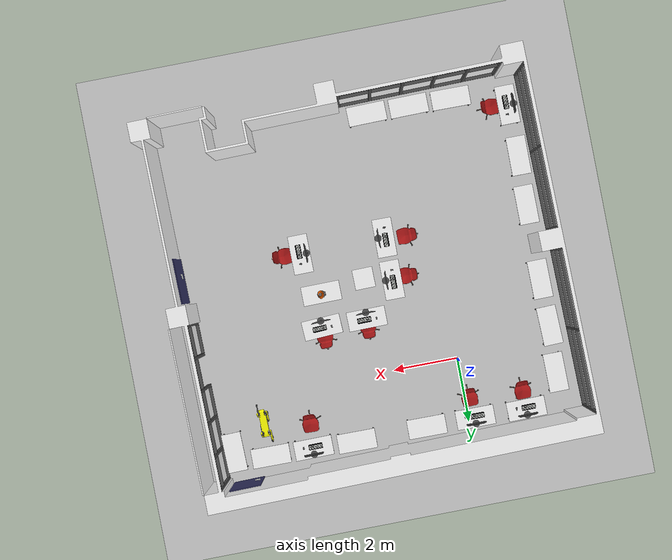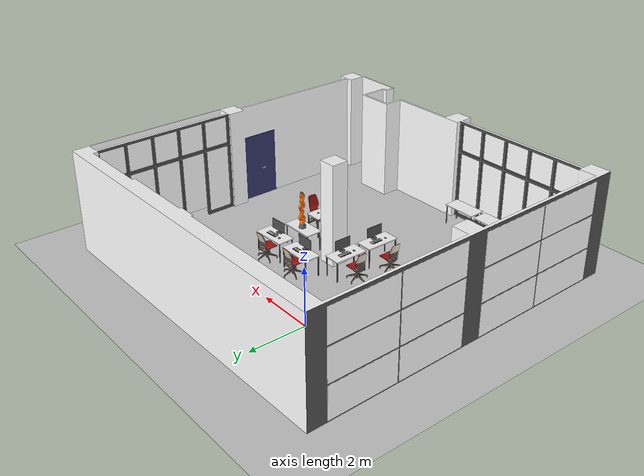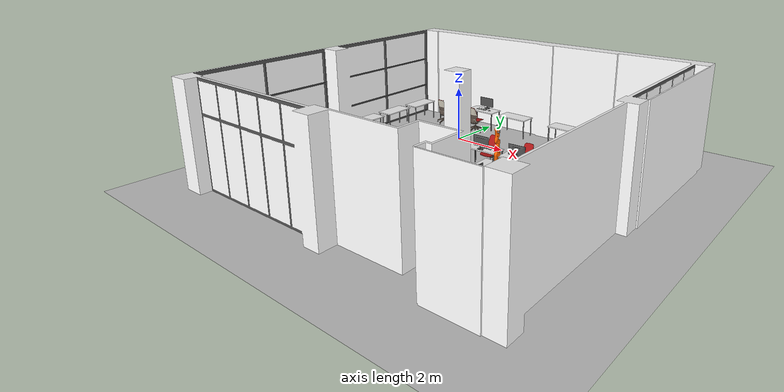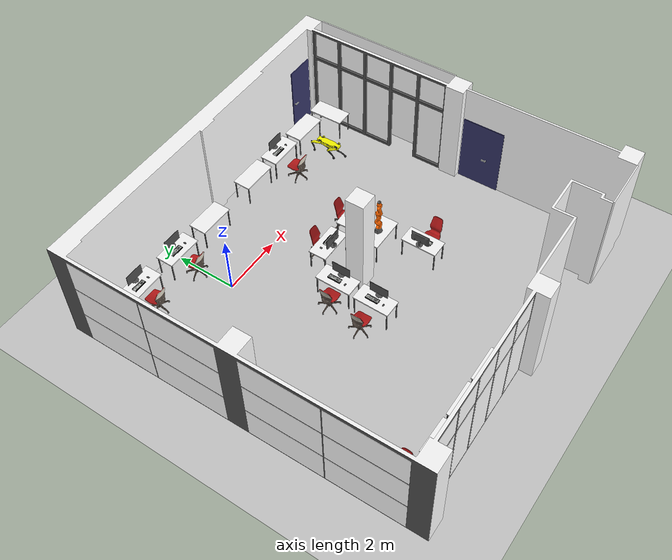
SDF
<sdf version="1.7">
 <world name="default">
  <light name="sun" type="directional">
   <pose>0 0 10 0 -0 0</pose>
   <diffuse>0.8 0.8 0.8 1</diffuse>
   <specular>0.2 0.2 0.2 1</specular>
   <attenuation>
    <range>1000</range>
    <constant>0.9</constant>
    <linear>0.01</linear>
    <quadratic>0.001</quadratic>
   </attenuation>
   <direction>-0.5 0.1 -0.9</direction>
   <spot><inner_angle>0</inner_angle><outer_angle>0</outer_angle><falloff>0</falloff></spot>
  </light>
  <model name="ground_plane">
   <static>1</static>
   <link name="link">
    <collision name="collision">
     <geometry><plane><normal>0 0 1</normal><size>100 100</size></plane></geometry>
     <surface>
      <contact><collide_bitmask>65535</collide_bitmask></contact>
      <friction><ode><mu>100</mu><mu2>50</mu2></ode></friction>
     </surface>
    </collision>
    <visual name="visual">
     <cast_shadows>0</cast_shadows>
     <geometry><plane><normal>0 0 1</normal><size>100 100</size></plane></geometry>
     <material>
      <script><uri>file://media/materials/scripts/gazebo.material</uri><name>Gazebo/Grey</name></script>
     </material>
    </visual>
   </link>
  </model>
  <gravity>0 0 -9.8</gravity>
  <magnetic_field>6e-06 2.3e-05 -4.2e-05</magnetic_field>
  <atmosphere type="adiabatic"/>
  <physics type="ode">
   <max_step_size>0.001</max_step_size>
   <real_time_factor>1</real_time_factor>
   <real_time_update_rate>1000</real_time_update_rate>
  </physics>
  <scene><ambient>0.4 0.4 0.4 1</ambient><background>0.7 0.7 0.7 1</background><shadows>1</shadows></scene>
  <spherical_coordinates>
   <surface_model>EARTH_WGS84</surface_model>
   <latitude_deg>0</latitude_deg>
   <longitude_deg>0</longitude_deg>
   <elevation>0</elevation>
   <heading_deg>0</heading_deg>
  </spherical_coordinates>
  <model name="stol_i_komp">
   <link name="link_1">
    <inertial>
     <mass>1</mass>
     <inertia>
      <ixx>0.166667</ixx>
      <ixy>0</ixy>
      <ixz>0</ixz>
      <iyy>0.166667</iyy>
      <iyz>0</iyz>
      <izz>0.166667</izz>
     </inertia>
    </inertial>
    <visual name="visual">
     <geometry>
      <mesh>
       <uri>/home/slaven/catkin_ws/src/my_simulations/models/meshes/stol_i_komp.dae</uri>
       <scale>1 1 1</scale>
      </mesh>
     </geometry>
    </visual>
    <collision name="collision">
     <geometry>
      <mesh>
       <uri>/home/slaven/catkin_ws/src/my_simulations/models/meshes/stol_i_komp.dae</uri>
       <scale>1 1 1</scale>
      </mesh>
     </geometry>
     <surface>
      <friction>
       <ode><mu>1</mu><mu2>1</mu2><fdir1>0 0 0</fdir1><slip1>0</slip1><slip2>0</slip2></ode>
       <torsional>
        <coefficient>1</coefficient>
        <patch_radius>0</patch_radius>
        <surface_radius>0</surface_radius>
        <use_patch_radius>1</use_patch_radius>
        <ode><slip>0</slip></ode>
       </torsional>
      </friction>
      <bounce><restitution_coefficient>0</restitution_coefficient><threshold>1e+06</threshold></bounce>
      <contact>
       <collide_without_contact>0</collide_without_contact>
       <collide_without_contact_bitmask>1</collide_without_contact_bitmask>
       <collide_bitmask>1</collide_bitmask>
       <ode>
        <soft_cfm>0</soft_cfm>
        <soft_erp>0.2</soft_erp>
        <kp>1e+13</kp>
        <kd>1</kd>
        <max_vel>0.01</max_vel>
        <min_depth>0</min_depth>
       </ode>
       <bullet>
        <split_impulse>1</split_impulse>
        <split_impulse_penetration_threshold>-0.01</split_impulse_penetration_threshold>
        <soft_cfm>0</soft_cfm>
        <soft_erp>0.2</soft_erp>
        <kp>1e+13</kp>
        <kd>1</kd>
       </bullet>
      </contact>
     </surface>
    </collision>
   </link>
   <static>0</static>
   <pose>1.5366 -2.81232 0.699999 -0 2e-06 1.56764</pose>
  </model>
  <model name="stol_i_komp_0">
   <link name="link_1">
    <inertial>
     <mass>1</mass>
     <inertia>
      <ixx>0.166667</ixx>
      <ixy>0</ixy>
      <ixz>0</ixz>
      <iyy>0.166667</iyy>
      <iyz>0</iyz>
      <izz>0.166667</izz>
     </inertia>
    </inertial>
    <visual name="visual">
     <geometry>
      <mesh>
       <uri>/home/slaven/catkin_ws/src/my_simulations/models/meshes/stol_i_komp.dae</uri>
       <scale>1 1 1</scale>
      </mesh>
     </geometry>
    </visual>
    <collision name="collision">
     <geometry>
      <mesh>
       <uri>/home/slaven/catkin_ws/src/my_simulations/models/meshes/stol_i_komp.dae</uri>
       <scale>1 1 1</scale>
      </mesh>
     </geometry>
     <surface>
      <friction>
       <ode><mu>1</mu><mu2>1</mu2><fdir1>0 0 0</fdir1><slip1>0</slip1><slip2>0</slip2></ode>
       <torsional>
        <coefficient>1</coefficient>
        <patch_radius>0</patch_radius>
        <surface_radius>0</surface_radius>
        <use_patch_radius>1</use_patch_radius>
        <ode><slip>0</slip></ode>
       </torsional>
      </friction>
      <bounce><restitution_coefficient>0</restitution_coefficient><threshold>1e+06</threshold></bounce>
      <contact>
       <collide_without_contact>0</collide_without_contact>
       <collide_without_contact_bitmask>1</collide_without_contact_bitmask>
       <collide_bitmask>1</collide_bitmask>
       <ode>
        <soft_cfm>0</soft_cfm>
        <soft_erp>0.2</soft_erp>
        <kp>1e+13</kp>
        <kd>1</kd>
        <max_vel>0.01</max_vel>
        <min_depth>0</min_depth>
       </ode>
       <bullet>
        <split_impulse>1</split_impulse>
        <split_impulse_penetration_threshold>-0.01</split_impulse_penetration_threshold>
        <soft_cfm>0</soft_cfm>
        <soft_erp>0.2</soft_erp>
        <kp>1e+13</kp>
        <kd>1</kd>
       </bullet>
      </contact>
     </surface>
    </collision>
   </link>
   <static>0</static>
   <pose>1.52345 -4.13796 0.699999 0 -2e-06 1.56027</pose>
  </model>
  <model name="stol_i_komp_1">
   <link name="link_1">
    <inertial>
     <mass>1</mass>
     <inertia>
      <ixx>0.166667</ixx>
      <ixy>0</ixy>
      <ixz>0</ixz>
      <iyy>0.166667</iyy>
      <iyz>0</iyz>
      <izz>0.166667</izz>
     </inertia>
    </inertial>
    <visual name="visual">
     <geometry>
      <mesh>
       <uri>/home/slaven/catkin_ws/src/my_simulations/models/meshes/stol_i_komp.dae</uri>
       <scale>1 1 1</scale>
      </mesh>
     </geometry>
    </visual>
    <collision name="collision">
     <geometry>
      <mesh>
       <uri>/home/slaven/catkin_ws/src/my_simulations/models/meshes/stol_i_komp.dae</uri>
       <scale>1 1 1</scale>
      </mesh>
     </geometry>
     <surface>
      <friction>
       <ode><mu>1</mu><mu2>1</mu2><fdir1>0 0 0</fdir1><slip1>0</slip1><slip2>0</slip2></ode>
       <torsional>
        <coefficient>1</coefficient>
        <patch_radius>0</patch_radius>
        <surface_radius>0</surface_radius>
        <use_patch_radius>1</use_patch_radius>
        <ode><slip>0</slip></ode>
       </torsional>
      </friction>
      <bounce><restitution_coefficient>0</restitution_coefficient><threshold>1e+06</threshold></bounce>
      <contact>
       <collide_without_contact>0</collide_without_contact>
       <collide_without_contact_bitmask>1</collide_without_contact_bitmask>
       <collide_bitmask>1</collide_bitmask>
       <ode>
        <soft_cfm>0</soft_cfm>
        <soft_erp>0.2</soft_erp>
        <kp>1e+13</kp>
        <kd>1</kd>
        <max_vel>0.01</max_vel>
        <min_depth>0</min_depth>
       </ode>
       <bullet>
        <split_impulse>1</split_impulse>
        <split_impulse_penetration_threshold>-0.01</split_impulse_penetration_threshold>
        <soft_cfm>0</soft_cfm>
        <soft_erp>0.2</soft_erp>
        <kp>1e+13</kp>
        <kd>1</kd>
       </bullet>
      </contact>
     </surface>
    </collision>
   </link>
   <static>0</static>
   <pose>3.94366 -1.78067 0.699999 0 -2e-06 0.051701</pose>
  </model>
  <model name="stol_i_komp_2">
   <link name="link_1">
    <inertial>
     <mass>1</mass>
     <inertia>
      <ixx>0.166667</ixx>
      <ixy>0</ixy>
      <ixz>0</ixz>
      <iyy>0.166667</iyy>
      <iyz>0</iyz>
      <izz>0.166667</izz>
     </inertia>
    </inertial>
    <visual name="visual">
     <geometry>
      <mesh>
       <uri>/home/slaven/catkin_ws/src/my_simulations/models/meshes/stol_i_komp.dae</uri>
       <scale>1 1 1</scale>
      </mesh>
     </geometry>
    </visual>
    <collision name="collision">
     <geometry>
      <mesh>
       <uri>/home/slaven/catkin_ws/src/my_simulations/models/meshes/stol_i_komp.dae</uri>
       <scale>1 1 1</scale>
      </mesh>
     </geometry>
     <surface>
      <friction>
       <ode><mu>1</mu><mu2>1</mu2><fdir1>0 0 0</fdir1><slip1>0</slip1><slip2>0</slip2></ode>
       <torsional>
        <coefficient>1</coefficient>
        <patch_radius>0</patch_radius>
        <surface_radius>0</surface_radius>
        <use_patch_radius>1</use_patch_radius>
        <ode><slip>0</slip></ode>
       </torsional>
      </friction>
      <bounce><restitution_coefficient>0</restitution_coefficient><threshold>1e+06</threshold></bounce>
      <contact>
       <collide_without_contact>0</collide_without_contact>
       <collide_without_contact_bitmask>1</collide_without_contact_bitmask>
       <collide_bitmask>1</collide_bitmask>
       <ode>
        <soft_cfm>0</soft_cfm>
        <soft_erp>0.2</soft_erp>
        <kp>1e+13</kp>
        <kd>1</kd>
        <max_vel>0.01</max_vel>
        <min_depth>0</min_depth>
       </ode>
       <bullet>
        <split_impulse>1</split_impulse>
        <split_impulse_penetration_threshold>-0.01</split_impulse_penetration_threshold>
        <soft_cfm>0</soft_cfm>
        <soft_erp>0.2</soft_erp>
        <kp>1e+13</kp>
        <kd>1</kd>
       </bullet>
      </contact>
     </surface>
    </collision>
   </link>
   <static>0</static>
   <pose>2.53198 -1.77767 0.699999 0 2e-06 0.009271</pose>
  </model>
  <model name="stol_i_komp_3">
   <link name="link_1">
    <inertial>
     <mass>1</mass>
     <inertia>
      <ixx>0.166667</ixx>
      <ixy>0</ixy>
      <ixz>0</ixz>
      <iyy>0.166667</iyy>
      <iyz>0</iyz>
      <izz>0.166667</izz>
     </inertia>
    </inertial>
    <visual name="visual">
     <geometry>
      <mesh>
       <uri>/home/slaven/catkin_ws/src/my_simulations/models/meshes/stol_i_komp.dae</uri>
       <scale>1 1 1</scale>
      </mesh>
     </geometry>
    </visual>
    <collision name="collision">
     <geometry>
      <mesh>
       <uri>/home/slaven/catkin_ws/src/my_simulations/models/meshes/stol_i_komp.dae</uri>
       <scale>1 1 1</scale>
      </mesh>
     </geometry>
     <surface>
      <friction>
       <ode><mu>1</mu><mu2>1</mu2><fdir1>0 0 0</fdir1><slip1>0</slip1><slip2>0</slip2></ode>
       <torsional>
        <coefficient>1</coefficient>
        <patch_radius>0</patch_radius>
        <surface_radius>0</surface_radius>
        <use_patch_radius>1</use_patch_radius>
        <ode><slip>0</slip></ode>
       </torsional>
      </friction>
      <bounce><restitution_coefficient>0</restitution_coefficient><threshold>1e+06</threshold></bounce>
      <contact>
       <collide_without_contact>0</collide_without_contact>
       <collide_without_contact_bitmask>1</collide_without_contact_bitmask>
       <collide_bitmask>1</collide_bitmask>
       <ode>
        <soft_cfm>0</soft_cfm>
        <soft_erp>0.2</soft_erp>
        <kp>1e+13</kp>
        <kd>1</kd>
        <max_vel>0.01</max_vel>
        <min_depth>0</min_depth>
       </ode>
       <bullet>
        <split_impulse>1</split_impulse>
        <split_impulse_penetration_threshold>-0.01</split_impulse_penetration_threshold>
        <soft_cfm>0</soft_cfm>
        <soft_erp>0.2</soft_erp>
        <kp>1e+13</kp>
        <kd>1</kd>
       </bullet>
      </contact>
     </surface>
    </collision>
   </link>
   <static>0</static>
   <pose>4.1732 -4.12466 0.699999 0 -2e-06 -1.56533</pose>
  </model>
  <model name="stol">
   <link name="link_0">
    <inertial>
     <mass>1</mass>
     <inertia>
      <ixx>0.166667</ixx>
      <ixy>0</ixy>
      <ixz>0</ixz>
      <iyy>0.166667</iyy>
      <iyz>0</iyz>
      <izz>0.166667</izz>
     </inertia>
    </inertial>
    <visual name="visual">
     <geometry>
      <mesh><uri>/home/slaven/catkin_ws/src/my_simulations/models/meshes/stol.dae</uri><scale>1 1 1</scale></mesh>
     </geometry>
    </visual>
    <collision name="collision">
     <geometry>
      <mesh><uri>/home/slaven/catkin_ws/src/my_simulations/models/meshes/stol.dae</uri><scale>1 1 1</scale></mesh>
     </geometry>
     <surface>
      <friction>
       <ode><mu>1</mu><mu2>1</mu2><fdir1>0 0 0</fdir1><slip1>0</slip1><slip2>0</slip2></ode>
       <torsional>
        <coefficient>1</coefficient>
        <patch_radius>0</patch_radius>
        <surface_radius>0</surface_radius>
        <use_patch_radius>1</use_patch_radius>
        <ode><slip>0</slip></ode>
       </torsional>
      </friction>
      <bounce><restitution_coefficient>0</restitution_coefficient><threshold>1e+06</threshold></bounce>
      <contact>
       <collide_without_contact>0</collide_without_contact>
       <collide_without_contact_bitmask>1</collide_without_contact_bitmask>
       <collide_bitmask>1</collide_bitmask>
       <ode>
        <soft_cfm>0</soft_cfm>
        <soft_erp>0.2</soft_erp>
        <kp>1e+13</kp>
        <kd>1</kd>
        <max_vel>0.01</max_vel>
        <min_depth>0</min_depth>
       </ode>
       <bullet>
        <split_impulse>1</split_impulse>
        <split_impulse_penetration_threshold>-0.01</split_impulse_penetration_threshold>
        <soft_cfm>0</soft_cfm>
        <soft_erp>0.2</soft_erp>
        <kp>1e+13</kp>
        <kd>1</kd>
       </bullet>
      </contact>
     </surface>
    </collision>
   </link>
   <static>0</static>
   <pose>3.76972 -2.81672 0.699999 0 -2e-06 0.005732</pose>
  </model>
  <model name="kuka">
   <link name="link_1">
    <inertial>
     <mass>1</mass>
     <inertia>
      <ixx>0.166667</ixx>
      <ixy>0</ixy>
      <ixz>0</ixz>
      <iyy>0.166667</iyy>
      <iyz>0</iyz>
      <izz>0.166667</izz>
     </inertia>
    </inertial>
    <pose>-0.00628 -0.063343 0.019073 0 -0 0</pose>
    <visual name="visual">
     <geometry>
      <mesh>
       <uri>/home/slaven/catkin_ws/src/my_simulations/models/meshes/LBR IIWA 14 R820.dae</uri>
       <scale>1 1 1</scale>
      </mesh>
     </geometry>
    </visual>
    <collision name="collision">
     <geometry>
      <mesh>
       <uri>/home/slaven/catkin_ws/src/my_simulations/models/meshes/LBR IIWA 14 R820.dae</uri>
       <scale>1 1 1</scale>
      </mesh>
     </geometry>
     <surface>
      <friction>
       <ode><mu>1</mu><mu2>1</mu2><fdir1>0 0 0</fdir1><slip1>0</slip1><slip2>0</slip2></ode>
       <torsional>
        <coefficient>1</coefficient>
        <patch_radius>0</patch_radius>
        <surface_radius>0</surface_radius>
        <use_patch_radius>1</use_patch_radius>
        <ode><slip>0</slip></ode>
       </torsional>
      </friction>
      <bounce><restitution_coefficient>0</restitution_coefficient><threshold>1e+06</threshold></bounce>
      <contact>
       <collide_without_contact>0</collide_without_contact>
       <collide_without_contact_bitmask>1</collide_without_contact_bitmask>
       <collide_bitmask>1</collide_bitmask>
       <ode>
        <soft_cfm>0</soft_cfm>
        <soft_erp>0.2</soft_erp>
        <kp>1e+13</kp>
        <kd>1</kd>
        <max_vel>0.01</max_vel>
        <min_depth>0</min_depth>
       </ode>
       <bullet>
        <split_impulse>1</split_impulse>
        <split_impulse_penetration_threshold>-0.01</split_impulse_penetration_threshold>
        <soft_cfm>0</soft_cfm>
        <soft_erp>0.2</soft_erp>
        <kp>1e+13</kp>
        <kd>1</kd>
       </bullet>
      </contact>
     </surface>
    </collision>
   </link>
   <static>0</static>
   <pose>3.77941 -2.71983 0.715929 -0 -2.6e-05 0.011747</pose>
  </model>
  <model name="zidovi3">
   <link name="link_0">
    <inertial>
     <mass>1</mass>
     <inertia>
      <ixx>0.166667</ixx>
      <ixy>0</ixy>
      <ixz>0</ixz>
      <iyy>0.166667</iyy>
      <iyz>0</iyz>
      <izz>0.166667</izz>
     </inertia>
    </inertial>
    <pose>-0 -2e-06 0 0 -0 0</pose>
    <visual name="visual">
     <geometry>
      <mesh>
       <uri>/home/slaven/catkin_ws/src/my_simulations/models/meshes/zidovi3.dae</uri>
       <scale>1 1 1</scale>
      </mesh>
     </geometry>
    </visual>
    <collision name="collision">
     <geometry>
      <mesh>
       <uri>/home/slaven/catkin_ws/src/my_simulations/models/meshes/zidovi3.dae</uri>
       <scale>1 1 1</scale>
      </mesh>
     </geometry>
     <surface>
      <friction>
       <ode><mu>1</mu><mu2>1</mu2><fdir1>0 0 0</fdir1><slip1>0</slip1><slip2>0</slip2></ode>
       <torsional>
        <coefficient>1</coefficient>
        <patch_radius>0</patch_radius>
        <surface_radius>0</surface_radius>
        <use_patch_radius>1</use_patch_radius>
        <ode><slip>0</slip></ode>
       </torsional>
      </friction>
      <bounce><restitution_coefficient>0</restitution_coefficient><threshold>1e+06</threshold></bounce>
      <contact>
       <collide_without_contact>0</collide_without_contact>
       <collide_without_contact_bitmask>1</collide_without_contact_bitmask>
       <collide_bitmask>1</collide_bitmask>
       <ode>
        <soft_cfm>0</soft_cfm>
        <soft_erp>0.2</soft_erp>
        <kp>1e+13</kp>
        <kd>1</kd>
        <max_vel>0.01</max_vel>
        <min_depth>0</min_depth>
       </ode>
       <bullet>
        <split_impulse>1</split_impulse>
        <split_impulse_penetration_threshold>-0.01</split_impulse_penetration_threshold>
        <soft_cfm>0</soft_cfm>
        <soft_erp>0.2</soft_erp>
        <kp>1e+13</kp>
        <kd>1</kd>
       </bullet>
      </contact>
     </surface>
    </collision>
   </link>
   <static>0</static>
   <pose>2.38925 -3.02063 -0 0 -0 0.013755</pose>
  </model>
  <model name="stol_i_komp_4">
   <link name="link_1">
    <inertial>
     <mass>1</mass>
     <inertia>
      <ixx>0.166667</ixx>
      <ixy>0</ixy>
      <ixz>0</ixz>
      <iyy>0.166667</iyy>
      <iyz>0</iyz>
      <izz>0.166667</izz>
     </inertia>
    </inertial>
    <visual name="visual">
     <geometry>
      <mesh>
       <uri>/home/slaven/catkin_ws/src/my_simulations/models/meshes/stol_i_komp.dae</uri>
       <scale>1 1 1</scale>
      </mesh>
     </geometry>
    </visual>
    <collision name="collision">
     <geometry>
      <mesh>
       <uri>/home/slaven/catkin_ws/src/my_simulations/models/meshes/stol_i_komp.dae</uri>
       <scale>1 1 1</scale>
      </mesh>
     </geometry>
     <surface>
      <friction>
       <ode><mu>1</mu><mu2>1</mu2><fdir1>0 0 0</fdir1><slip1>0</slip1><slip2>0</slip2></ode>
       <torsional>
        <coefficient>1</coefficient>
        <patch_radius>0</patch_radius>
        <surface_radius>0</surface_radius>
        <use_patch_radius>1</use_patch_radius>
        <ode><slip>0</slip></ode>
       </torsional>
      </friction>
      <bounce><restitution_coefficient>0</restitution_coefficient><threshold>1e+06</threshold></bounce>
      <contact>
       <collide_without_contact>0</collide_without_contact>
       <collide_without_contact_bitmask>1</collide_without_contact_bitmask>
       <collide_bitmask>1</collide_bitmask>
       <ode>
        <soft_cfm>0</soft_cfm>
        <soft_erp>0.2</soft_erp>
        <kp>1e+13</kp>
        <kd>1</kd>
        <max_vel>0.01</max_vel>
        <min_depth>0</min_depth>
       </ode>
       <bullet>
        <split_impulse>1</split_impulse>
        <split_impulse_penetration_threshold>-0.01</split_impulse_penetration_threshold>
        <soft_cfm>0</soft_cfm>
        <soft_erp>0.2</soft_erp>
        <kp>1e+13</kp>
        <kd>1</kd>
       </bullet>
      </contact>
     </surface>
    </collision>
   </link>
   <static>0</static>
   <pose>-0.18708 1.85961 0.699999 0 -2e-06 3.13569</pose>
  </model>
  <model name="stol_i_komp_5">
   <link name="link_1">
    <inertial>
     <mass>1</mass>
     <inertia>
      <ixx>0.166667</ixx>
      <ixy>0</ixy>
      <ixz>0</ixz>
      <iyy>0.166667</iyy>
      <iyz>0</iyz>
      <izz>0.166667</izz>
     </inertia>
    </inertial>
    <visual name="visual">
     <geometry>
      <mesh>
       <uri>/home/slaven/catkin_ws/src/my_simulations/models/meshes/stol_i_komp.dae</uri>
       <scale>1 1 1</scale>
      </mesh>
     </geometry>
    </visual>
    <collision name="collision">
     <geometry>
      <mesh>
       <uri>/home/slaven/catkin_ws/src/my_simulations/models/meshes/stol_i_komp.dae</uri>
       <scale>1 1 1</scale>
      </mesh>
     </geometry>
     <surface>
      <friction>
       <ode><mu>1</mu><mu2>1</mu2><fdir1>0 0 0</fdir1><slip1>0</slip1><slip2>0</slip2></ode>
       <torsional>
        <coefficient>1</coefficient>
        <patch_radius>0</patch_radius>
        <surface_radius>0</surface_radius>
        <use_patch_radius>1</use_patch_radius>
        <ode><slip>0</slip></ode>
       </torsional>
      </friction>
      <bounce><restitution_coefficient>0</restitution_coefficient><threshold>1e+06</threshold></bounce>
      <contact>
       <collide_without_contact>0</collide_without_contact>
       <collide_without_contact_bitmask>1</collide_without_contact_bitmask>
       <collide_bitmask>1</collide_bitmask>
       <ode>
        <soft_cfm>0</soft_cfm>
        <soft_erp>0.2</soft_erp>
        <kp>1e+13</kp>
        <kd>1</kd>
        <max_vel>0.01</max_vel>
        <min_depth>0</min_depth>
       </ode>
       <bullet>
        <split_impulse>1</split_impulse>
        <split_impulse_penetration_threshold>-0.01</split_impulse_penetration_threshold>
        <soft_cfm>0</soft_cfm>
        <soft_erp>0.2</soft_erp>
        <kp>1e+13</kp>
        <kd>1</kd>
       </bullet>
      </contact>
     </surface>
    </collision>
   </link>
   <static>0</static>
   <pose>4.91228 1.84464 0.699999 0 2e-06 -3.13605</pose>
  </model>
  <model name="stol_0">
   <link name="link_0">
    <inertial>
     <mass>1</mass>
     <inertia>
      <ixx>0.166667</ixx>
      <ixy>0</ixy>
      <ixz>0</ixz>
      <iyy>0.166667</iyy>
      <iyz>0</iyz>
      <izz>0.166667</izz>
     </inertia>
    </inertial>
    <visual name="visual">
     <geometry>
      <mesh><uri>/home/slaven/catkin_ws/src/my_simulations/models/meshes/stol.dae</uri><scale>1 1 1</scale></mesh>
     </geometry>
    </visual>
    <collision name="collision">
     <geometry>
      <mesh><uri>/home/slaven/catkin_ws/src/my_simulations/models/meshes/stol.dae</uri><scale>1 1 1</scale></mesh>
     </geometry>
     <surface>
      <friction>
       <ode><mu>1</mu><mu2>1</mu2><fdir1>0 0 0</fdir1><slip1>0</slip1><slip2>0</slip2></ode>
       <torsional>
        <coefficient>1</coefficient>
        <patch_radius>0</patch_radius>
        <surface_radius>0</surface_radius>
        <use_patch_radius>1</use_patch_radius>
        <ode><slip>0</slip></ode>
       </torsional>
      </friction>
      <bounce><restitution_coefficient>0</restitution_coefficient><threshold>1e+06</threshold></bounce>
      <contact>
       <collide_without_contact>0</collide_without_contact>
       <collide_without_contact_bitmask>1</collide_without_contact_bitmask>
       <collide_bitmask>1</collide_bitmask>
       <ode>
        <soft_cfm>0</soft_cfm>
        <soft_erp>0.2</soft_erp>
        <kp>1e+13</kp>
        <kd>1</kd>
        <max_vel>0.01</max_vel>
        <min_depth>0</min_depth>
       </ode>
       <bullet>
        <split_impulse>1</split_impulse>
        <split_impulse_penetration_threshold>-0.01</split_impulse_penetration_threshold>
        <soft_cfm>0</soft_cfm>
        <soft_erp>0.2</soft_erp>
        <kp>1e+13</kp>
        <kd>1</kd>
       </bullet>
      </contact>
     </surface>
    </collision>
   </link>
   <static>0</static>
   <pose>-3.03737 -5.84714 0.699999 1e-06 -1e-06 1.56576</pose>
  </model>
  <model name="stol_1">
   <link name="link_0">
    <inertial>
     <mass>1</mass>
     <inertia>
      <ixx>0.166667</ixx>
      <ixy>0</ixy>
      <ixz>0</ixz>
      <iyy>0.166667</iyy>
      <iyz>0</iyz>
      <izz>0.166667</izz>
     </inertia>
    </inertial>
    <visual name="visual">
     <geometry>
      <mesh><uri>/home/slaven/catkin_ws/src/my_simulations/models/meshes/stol.dae</uri><scale>1 1 1</scale></mesh>
     </geometry>
    </visual>
    <collision name="collision">
     <geometry>
      <mesh><uri>/home/slaven/catkin_ws/src/my_simulations/models/meshes/stol.dae</uri><scale>1 1 1</scale></mesh>
     </geometry>
     <surface>
      <friction>
       <ode><mu>1</mu><mu2>1</mu2><fdir1>0 0 0</fdir1><slip1>0</slip1><slip2>0</slip2></ode>
       <torsional>
        <coefficient>1</coefficient>
        <patch_radius>0</patch_radius>
        <surface_radius>0</surface_radius>
        <use_patch_radius>1</use_patch_radius>
        <ode><slip>0</slip></ode>
       </torsional>
      </friction>
      <bounce><restitution_coefficient>0</restitution_coefficient><threshold>1e+06</threshold></bounce>
      <contact>
       <collide_without_contact>0</collide_without_contact>
       <collide_without_contact_bitmask>1</collide_without_contact_bitmask>
       <collide_bitmask>1</collide_bitmask>
       <ode>
        <soft_cfm>0</soft_cfm>
        <soft_erp>0.2</soft_erp>
        <kp>1e+13</kp>
        <kd>1</kd>
        <max_vel>0.01</max_vel>
        <min_depth>0</min_depth>
       </ode>
       <bullet>
        <split_impulse>1</split_impulse>
        <split_impulse_penetration_threshold>-0.01</split_impulse_penetration_threshold>
        <soft_cfm>0</soft_cfm>
        <soft_erp>0.2</soft_erp>
        <kp>1e+13</kp>
        <kd>1</kd>
       </bullet>
      </contact>
     </surface>
    </collision>
   </link>
   <static>0</static>
   <pose>-2.98575 -4.3109 0.699999 0 -2e-06 1.57339</pose>
  </model>
  <model name="stol_2">
   <link name="link_0">
    <inertial>
     <mass>1</mass>
     <inertia>
      <ixx>0.166667</ixx>
      <ixy>0</ixy>
      <ixz>0</ixz>
      <iyy>0.166667</iyy>
      <iyz>0</iyz>
      <izz>0.166667</izz>
     </inertia>
    </inertial>
    <visual name="visual">
     <geometry>
      <mesh><uri>/home/slaven/catkin_ws/src/my_simulations/models/meshes/stol.dae</uri><scale>1 1 1</scale></mesh>
     </geometry>
    </visual>
    <collision name="collision">
     <geometry>
      <mesh><uri>/home/slaven/catkin_ws/src/my_simulations/models/meshes/stol.dae</uri><scale>1 1 1</scale></mesh>
     </geometry>
     <surface>
      <friction>
       <ode><mu>1</mu><mu2>1</mu2><fdir1>0 0 0</fdir1><slip1>0</slip1><slip2>0</slip2></ode>
       <torsional>
        <coefficient>1</coefficient>
        <patch_radius>0</patch_radius>
        <surface_radius>0</surface_radius>
        <use_patch_radius>1</use_patch_radius>
        <ode><slip>0</slip></ode>
       </torsional>
      </friction>
      <bounce><restitution_coefficient>0</restitution_coefficient><threshold>1e+06</threshold></bounce>
      <contact>
       <collide_without_contact>0</collide_without_contact>
       <collide_without_contact_bitmask>1</collide_without_contact_bitmask>
       <collide_bitmask>1</collide_bitmask>
       <ode>
        <soft_cfm>0</soft_cfm>
        <soft_erp>0.2</soft_erp>
        <kp>1e+13</kp>
        <kd>1</kd>
        <max_vel>0.01</max_vel>
        <min_depth>0</min_depth>
       </ode>
       <bullet>
        <split_impulse>1</split_impulse>
        <split_impulse_penetration_threshold>-0.01</split_impulse_penetration_threshold>
        <soft_cfm>0</soft_cfm>
        <soft_erp>0.2</soft_erp>
        <kp>1e+13</kp>
        <kd>1</kd>
       </bullet>
      </contact>
     </surface>
    </collision>
   </link>
   <static>0</static>
   <pose>-2.96415 -1.96662 0.699999 0 2e-06 -1.56358</pose>
  </model>
  <model name="stol_3">
   <link name="link_0">
    <inertial>
     <mass>1</mass>
     <inertia>
      <ixx>0.166667</ixx>
      <ixy>0</ixy>
      <ixz>0</ixz>
      <iyy>0.166667</iyy>
      <iyz>0</iyz>
      <izz>0.166667</izz>
     </inertia>
    </inertial>
    <visual name="visual">
     <geometry>
      <mesh><uri>/home/slaven/catkin_ws/src/my_simulations/models/meshes/stol.dae</uri><scale>1 1 1</scale></mesh>
     </geometry>
    </visual>
    <collision name="collision">
     <geometry>
      <mesh><uri>/home/slaven/catkin_ws/src/my_simulations/models/meshes/stol.dae</uri><scale>1 1 1</scale></mesh>
     </geometry>
     <surface>
      <friction>
       <ode><mu>1</mu><mu2>1</mu2><fdir1>0 0 0</fdir1><slip1>0</slip1><slip2>0</slip2></ode>
       <torsional>
        <coefficient>1</coefficient>
        <patch_radius>0</patch_radius>
        <surface_radius>0</surface_radius>
        <use_patch_radius>1</use_patch_radius>
        <ode><slip>0</slip></ode>
       </torsional>
      </friction>
      <bounce><restitution_coefficient>0</restitution_coefficient><threshold>1e+06</threshold></bounce>
      <contact>
       <collide_without_contact>0</collide_without_contact>
       <collide_without_contact_bitmask>1</collide_without_contact_bitmask>
       <collide_bitmask>1</collide_bitmask>
       <ode>
        <soft_cfm>0</soft_cfm>
        <soft_erp>0.2</soft_erp>
        <kp>1e+13</kp>
        <kd>1</kd>
        <max_vel>0.01</max_vel>
        <min_depth>0</min_depth>
       </ode>
       <bullet>
        <split_impulse>1</split_impulse>
        <split_impulse_penetration_threshold>-0.01</split_impulse_penetration_threshold>
        <soft_cfm>0</soft_cfm>
        <soft_erp>0.2</soft_erp>
        <kp>1e+13</kp>
        <kd>1</kd>
       </bullet>
      </contact>
     </surface>
    </collision>
   </link>
   <static>0</static>
   <pose>-2.98458 -0.496556 0.699999 0 2e-06 1.60049</pose>
  </model>
  <model name="stol_i_komp_6">
   <link name="link_1">
    <inertial>
     <mass>1</mass>
     <inertia>
      <ixx>0.166667</ixx>
      <ixy>0</ixy>
      <ixz>0</ixz>
      <iyy>0.166667</iyy>
      <iyz>0</iyz>
      <izz>0.166667</izz>
     </inertia>
    </inertial>
    <visual name="visual">
     <geometry>
      <mesh>
       <uri>/home/slaven/catkin_ws/src/my_simulations/models/meshes/stol_i_komp.dae</uri>
       <scale>1 1 1</scale>
      </mesh>
     </geometry>
    </visual>
    <collision name="collision">
     <geometry>
      <mesh>
       <uri>/home/slaven/catkin_ws/src/my_simulations/models/meshes/stol_i_komp.dae</uri>
       <scale>1 1 1</scale>
      </mesh>
     </geometry>
     <surface>
      <friction>
       <ode><mu>1</mu><mu2>1</mu2><fdir1>0 0 0</fdir1><slip1>0</slip1><slip2>0</slip2></ode>
       <torsional>
        <coefficient>1</coefficient>
        <patch_radius>0</patch_radius>
        <surface_radius>0</surface_radius>
        <use_patch_radius>1</use_patch_radius>
        <ode><slip>0</slip></ode>
       </torsional>
      </friction>
      <bounce><restitution_coefficient>0</restitution_coefficient><threshold>1e+06</threshold></bounce>
      <contact>
       <collide_without_contact>0</collide_without_contact>
       <collide_without_contact_bitmask>1</collide_without_contact_bitmask>
       <collide_bitmask>1</collide_bitmask>
       <ode>
        <soft_cfm>0</soft_cfm>
        <soft_erp>0.2</soft_erp>
        <kp>1e+13</kp>
        <kd>1</kd>
        <max_vel>0.01</max_vel>
        <min_depth>0</min_depth>
       </ode>
       <bullet>
        <split_impulse>1</split_impulse>
        <split_impulse_penetration_threshold>-0.01</split_impulse_penetration_threshold>
        <soft_cfm>0</soft_cfm>
        <soft_erp>0.2</soft_erp>
        <kp>1e+13</kp>
        <kd>1</kd>
       </bullet>
      </contact>
     </surface>
    </collision>
   </link>
   <static>0</static>
   <pose>-2.99482 -7.4602 0.699999 0 2e-06 -1.56543</pose>
  </model>
  <model name="stol_4">
   <link name="link_0">
    <inertial>
     <mass>1</mass>
     <inertia>
      <ixx>0.166667</ixx>
      <ixy>0</ixy>
      <ixz>0</ixz>
      <iyy>0.166667</iyy>
      <iyz>0</iyz>
      <izz>0.166667</izz>
     </inertia>
    </inertial>
    <visual name="visual">
     <geometry>
      <mesh><uri>/home/slaven/catkin_ws/src/my_simulations/models/meshes/stol.dae</uri><scale>1 1 1</scale></mesh>
     </geometry>
    </visual>
    <collision name="collision">
     <geometry>
      <mesh><uri>/home/slaven/catkin_ws/src/my_simulations/models/meshes/stol.dae</uri><scale>1 1 1</scale></mesh>
     </geometry>
     <surface>
      <friction>
       <ode><mu>1</mu><mu2>1</mu2><fdir1>0 0 0</fdir1><slip1>0</slip1><slip2>0</slip2></ode>
       <torsional>
        <coefficient>1</coefficient>
        <patch_radius>0</patch_radius>
        <surface_radius>0</surface_radius>
        <use_patch_radius>1</use_patch_radius>
        <ode><slip>0</slip></ode>
       </torsional>
      </friction>
      <bounce><restitution_coefficient>0</restitution_coefficient><threshold>1e+06</threshold></bounce>
      <contact>
       <collide_without_contact>0</collide_without_contact>
       <collide_without_contact_bitmask>1</collide_without_contact_bitmask>
       <collide_bitmask>1</collide_bitmask>
       <ode>
        <soft_cfm>0</soft_cfm>
        <soft_erp>0.2</soft_erp>
        <kp>1e+13</kp>
        <kd>1</kd>
        <max_vel>0.01</max_vel>
        <min_depth>0</min_depth>
       </ode>
       <bullet>
        <split_impulse>1</split_impulse>
        <split_impulse_penetration_threshold>-0.01</split_impulse_penetration_threshold>
        <soft_cfm>0</soft_cfm>
        <soft_erp>0.2</soft_erp>
        <kp>1e+13</kp>
        <kd>1</kd>
       </bullet>
      </contact>
     </surface>
    </collision>
   </link>
   <static>0</static>
   <pose>-2.89879 0.954753 0.699998 1e-06 4e-06 1.57652</pose>
  </model>
  <model name="stol_i_komp_7">
   <link name="link_1">
    <inertial>
     <mass>1</mass>
     <inertia>
      <ixx>0.166667</ixx>
      <ixy>0</ixy>
      <ixz>0</ixz>
      <iyy>0.166667</iyy>
      <iyz>0</iyz>
      <izz>0.166667</izz>
     </inertia>
    </inertial>
    <visual name="visual">
     <geometry>
      <mesh>
       <uri>/home/slaven/catkin_ws/src/my_simulations/models/meshes/stol_i_komp.dae</uri>
       <scale>1 1 1</scale>
      </mesh>
     </geometry>
    </visual>
    <collision name="collision">
     <geometry>
      <mesh>
       <uri>/home/slaven/catkin_ws/src/my_simulations/models/meshes/stol_i_komp.dae</uri>
       <scale>1 1 1</scale>
      </mesh>
     </geometry>
     <surface>
      <friction>
       <ode><mu>1</mu><mu2>1</mu2><fdir1>0 0 0</fdir1><slip1>0</slip1><slip2>0</slip2></ode>
       <torsional>
        <coefficient>1</coefficient>
        <patch_radius>0</patch_radius>
        <surface_radius>0</surface_radius>
        <use_patch_radius>1</use_patch_radius>
        <ode><slip>0</slip></ode>
       </torsional>
      </friction>
      <bounce><restitution_coefficient>0</restitution_coefficient><threshold>1e+06</threshold></bounce>
      <contact>
       <collide_without_contact>0</collide_without_contact>
       <collide_without_contact_bitmask>1</collide_without_contact_bitmask>
       <collide_bitmask>1</collide_bitmask>
       <ode>
        <soft_cfm>0</soft_cfm>
        <soft_erp>0.2</soft_erp>
        <kp>1e+13</kp>
        <kd>1</kd>
        <max_vel>0.01</max_vel>
        <min_depth>0</min_depth>
       </ode>
       <bullet>
        <split_impulse>1</split_impulse>
        <split_impulse_penetration_threshold>-0.01</split_impulse_penetration_threshold>
        <soft_cfm>0</soft_cfm>
        <soft_erp>0.2</soft_erp>
        <kp>1e+13</kp>
        <kd>1</kd>
       </bullet>
      </contact>
     </surface>
    </collision>
   </link>
   <static>0</static>
   <pose>-1.79447 1.89417 0.699999 0 2e-06 -3.13231</pose>
  </model>
  <model name="stol_5">
   <link name="link_0">
    <inertial>
     <mass>1</mass>
     <inertia>
      <ixx>0.166667</ixx>
      <ixy>0</ixy>
      <ixz>0</ixz>
      <iyy>0.166667</iyy>
      <iyz>0</iyz>
      <izz>0.166667</izz>
     </inertia>
    </inertial>
    <visual name="visual">
     <geometry>
      <mesh><uri>/home/slaven/catkin_ws/src/my_simulations/models/meshes/stol.dae</uri><scale>1 1 1</scale></mesh>
     </geometry>
    </visual>
    <collision name="collision">
     <geometry>
      <mesh><uri>/home/slaven/catkin_ws/src/my_simulations/models/meshes/stol.dae</uri><scale>1 1 1</scale></mesh>
     </geometry>
     <surface>
      <friction>
       <ode><mu>1</mu><mu2>1</mu2><fdir1>0 0 0</fdir1><slip1>0</slip1><slip2>0</slip2></ode>
       <torsional>
        <coefficient>1</coefficient>
        <patch_radius>0</patch_radius>
        <surface_radius>0</surface_radius>
        <use_patch_radius>1</use_patch_radius>
        <ode><slip>0</slip></ode>
       </torsional>
      </friction>
      <bounce><restitution_coefficient>0</restitution_coefficient><threshold>1e+06</threshold></bounce>
      <contact>
       <collide_without_contact>0</collide_without_contact>
       <collide_without_contact_bitmask>1</collide_without_contact_bitmask>
       <collide_bitmask>1</collide_bitmask>
       <ode>
        <soft_cfm>0</soft_cfm>
        <soft_erp>0.2</soft_erp>
        <kp>1e+13</kp>
        <kd>1</kd>
        <max_vel>0.01</max_vel>
        <min_depth>0</min_depth>
       </ode>
       <bullet>
        <split_impulse>1</split_impulse>
        <split_impulse_penetration_threshold>-0.01</split_impulse_penetration_threshold>
        <soft_cfm>0</soft_cfm>
        <soft_erp>0.2</soft_erp>
        <kp>1e+13</kp>
        <kd>1</kd>
       </bullet>
      </contact>
     </surface>
    </collision>
   </link>
   <static>0</static>
   <pose>1.34028 1.85941 0.699999 0 -2e-06 -0.008468</pose>
  </model>
  <model name="stol_6">
   <link name="link_0">
    <inertial>
     <mass>1</mass>
     <inertia>
      <ixx>0.166667</ixx>
      <ixy>0</ixy>
      <ixz>0</ixz>
      <iyy>0.166667</iyy>
      <iyz>0</iyz>
      <izz>0.166667</izz>
     </inertia>
    </inertial>
    <visual name="visual">
     <geometry>
      <mesh><uri>/home/slaven/catkin_ws/src/my_simulations/models/meshes/stol.dae</uri><scale>1 1 1</scale></mesh>
     </geometry>
    </visual>
    <collision name="collision">
     <geometry>
      <mesh><uri>/home/slaven/catkin_ws/src/my_simulations/models/meshes/stol.dae</uri><scale>1 1 1</scale></mesh>
     </geometry>
     <surface>
      <friction>
       <ode><mu>1</mu><mu2>1</mu2><fdir1>0 0 0</fdir1><slip1>0</slip1><slip2>0</slip2></ode>
       <torsional>
        <coefficient>1</coefficient>
        <patch_radius>0</patch_radius>
        <surface_radius>0</surface_radius>
        <use_patch_radius>1</use_patch_radius>
        <ode><slip>0</slip></ode>
       </torsional>
      </friction>
      <bounce><restitution_coefficient>0</restitution_coefficient><threshold>1e+06</threshold></bounce>
      <contact>
       <collide_without_contact>0</collide_without_contact>
       <collide_without_contact_bitmask>1</collide_without_contact_bitmask>
       <collide_bitmask>1</collide_bitmask>
       <ode>
        <soft_cfm>0</soft_cfm>
        <soft_erp>0.2</soft_erp>
        <kp>1e+13</kp>
        <kd>1</kd>
        <max_vel>0.01</max_vel>
        <min_depth>0</min_depth>
       </ode>
       <bullet>
        <split_impulse>1</split_impulse>
        <split_impulse_penetration_threshold>-0.01</split_impulse_penetration_threshold>
        <soft_cfm>0</soft_cfm>
        <soft_erp>0.2</soft_erp>
        <kp>1e+13</kp>
        <kd>1</kd>
       </bullet>
      </contact>
     </surface>
    </collision>
   </link>
   <static>0</static>
   <pose>3.55228 1.88847 0.699999 0 -2e-06 -0.006371</pose>
  </model>
  <model name="stol_7">
   <link name="link_0">
    <inertial>
     <mass>1</mass>
     <inertia>
      <ixx>0.166667</ixx>
      <ixy>0</ixy>
      <ixz>0</ixz>
      <iyy>0.166667</iyy>
      <iyz>0</iyz>
      <izz>0.166667</izz>
     </inertia>
    </inertial>
    <visual name="visual">
     <geometry>
      <mesh><uri>/home/slaven/catkin_ws/src/my_simulations/models/meshes/stol.dae</uri><scale>1 1 1</scale></mesh>
     </geometry>
    </visual>
    <collision name="collision">
     <geometry>
      <mesh><uri>/home/slaven/catkin_ws/src/my_simulations/models/meshes/stol.dae</uri><scale>1 1 1</scale></mesh>
     </geometry>
     <surface>
      <friction>
       <ode><mu>1</mu><mu2>1</mu2><fdir1>0 0 0</fdir1><slip1>0</slip1><slip2>0</slip2></ode>
       <torsional>
        <coefficient>1</coefficient>
        <patch_radius>0</patch_radius>
        <surface_radius>0</surface_radius>
        <use_patch_radius>1</use_patch_radius>
        <ode><slip>0</slip></ode>
       </torsional>
      </friction>
      <bounce><restitution_coefficient>0</restitution_coefficient><threshold>1e+06</threshold></bounce>
      <contact>
       <collide_without_contact>0</collide_without_contact>
       <collide_without_contact_bitmask>1</collide_without_contact_bitmask>
       <collide_bitmask>1</collide_bitmask>
       <ode>
        <soft_cfm>0</soft_cfm>
        <soft_erp>0.2</soft_erp>
        <kp>1e+13</kp>
        <kd>1</kd>
        <max_vel>0.01</max_vel>
        <min_depth>0</min_depth>
       </ode>
       <bullet>
        <split_impulse>1</split_impulse>
        <split_impulse_penetration_threshold>-0.01</split_impulse_penetration_threshold>
        <soft_cfm>0</soft_cfm>
        <soft_erp>0.2</soft_erp>
        <kp>1e+13</kp>
        <kd>1</kd>
       </bullet>
      </contact>
     </surface>
    </collision>
   </link>
   <static>0</static>
   <pose>6.25359 1.83429 0.699999 -0 2e-06 -0.008669</pose>
  </model>
  <model name="stol_8">
   <link name="link_0">
    <inertial>
     <mass>1</mass>
     <inertia>
      <ixx>0.166667</ixx>
      <ixy>0</ixy>
      <ixz>0</ixz>
      <iyy>0.166667</iyy>
      <iyz>0</iyz>
      <izz>0.166667</izz>
     </inertia>
    </inertial>
    <visual name="visual">
     <geometry>
      <mesh><uri>/home/slaven/catkin_ws/src/my_simulations/models/meshes/stol.dae</uri><scale>1 1 1</scale></mesh>
     </geometry>
    </visual>
    <collision name="collision">
     <geometry>
      <mesh><uri>/home/slaven/catkin_ws/src/my_simulations/models/meshes/stol.dae</uri><scale>1 1 1</scale></mesh>
     </geometry>
     <surface>
      <friction>
       <ode><mu>1</mu><mu2>1</mu2><fdir1>0 0 0</fdir1><slip1>0</slip1><slip2>0</slip2></ode>
       <torsional>
        <coefficient>1</coefficient>
        <patch_radius>0</patch_radius>
        <surface_radius>0</surface_radius>
        <use_patch_radius>1</use_patch_radius>
        <ode><slip>0</slip></ode>
       </torsional>
      </friction>
      <bounce><restitution_coefficient>0</restitution_coefficient><threshold>1e+06</threshold></bounce>
      <contact>
       <collide_without_contact>0</collide_without_contact>
       <collide_without_contact_bitmask>1</collide_without_contact_bitmask>
       <collide_bitmask>1</collide_bitmask>
       <ode>
        <soft_cfm>0</soft_cfm>
        <soft_erp>0.2</soft_erp>
        <kp>1e+13</kp>
        <kd>1</kd>
        <max_vel>0.01</max_vel>
        <min_depth>0</min_depth>
       </ode>
       <bullet>
        <split_impulse>1</split_impulse>
        <split_impulse_penetration_threshold>-0.01</split_impulse_penetration_threshold>
        <soft_cfm>0</soft_cfm>
        <soft_erp>0.2</soft_erp>
        <kp>1e+13</kp>
        <kd>1</kd>
       </bullet>
      </contact>
     </surface>
    </collision>
   </link>
   <static>0</static>
   <pose>7.3448 1.51242 0.699999 0 -2e-06 -1.54916</pose>
  </model>
  <model name="spot">
   <link name="link_0">
    <inertial>
     <mass>1</mass>
     <inertia>
      <ixx>0.166667</ixx>
      <ixy>0</ixy>
      <ixz>0</ixz>
      <iyy>0.166667</iyy>
      <iyz>0</iyz>
      <izz>0.166667</izz>
     </inertia>
    </inertial>
    <pose>0 -0 -0 1.57362 -0 0</pose>
    <visual name="visual">
     <geometry>
      <mesh><uri>/home/slaven/catkin_ws/src/my_simulations/models/meshes/spot.dae</uri><scale>1 1 1</scale></mesh>
     </geometry>
    </visual>
    <collision name="collision">
     <geometry>
      <mesh><uri>/home/slaven/catkin_ws/src/my_simulations/models/meshes/spot.dae</uri><scale>1 1 1</scale></mesh>
     </geometry>
     <surface>
      <friction>
       <ode><mu>1</mu><mu2>1</mu2><fdir1>0 0 0</fdir1><slip1>0</slip1><slip2>0</slip2></ode>
       <torsional>
        <coefficient>1</coefficient>
        <patch_radius>0</patch_radius>
        <surface_radius>0</surface_radius>
        <use_patch_radius>1</use_patch_radius>
        <ode><slip>0</slip></ode>
       </torsional>
      </friction>
      <bounce><restitution_coefficient>0</restitution_coefficient><threshold>1e+06</threshold></bounce>
      <contact>
       <collide_without_contact>0</collide_without_contact>
       <collide_without_contact_bitmask>1</collide_without_contact_bitmask>
       <collide_bitmask>1</collide_bitmask>
       <ode>
        <soft_cfm>0</soft_cfm>
        <soft_erp>0.2</soft_erp>
        <kp>1e+13</kp>
        <kd>1</kd>
        <max_vel>0.01</max_vel>
        <min_depth>0</min_depth>
       </ode>
       <bullet>
        <split_impulse>1</split_impulse>
        <split_impulse_penetration_threshold>-0.01</split_impulse_penetration_threshold>
        <soft_cfm>0</soft_cfm>
        <soft_erp>0.2</soft_erp>
        <kp>1e+13</kp>
        <kd>1</kd>
       </bullet>
      </contact>
     </surface>
    </collision>
   </link>
   <static>0</static>
   <pose>6.28781 0.723523 0.423671 -0.0028 -0.000227 0.0299</pose>
  </model>
  <model name="stolac">
   <link name="link_0">
    <inertial>
     <mass>1</mass>
     <inertia>
      <ixx>0.166667</ixx>
      <ixy>0</ixy>
      <ixz>0</ixz>
      <iyy>0.166667</iyy>
      <iyz>0</iyz>
      <izz>0.166667</izz>
     </inertia>
    </inertial>
    <pose>0 0 0 1.60577 -0 0</pose>
    <visual name="visual">
     <geometry>
      <mesh><uri>/home/slaven/catkin_ws/src/my_simulations/models/meshes/stolac.dae</uri><scale>1 1 1</scale></mesh>
     </geometry>
    </visual>
    <collision name="collision">
     <geometry>
      <mesh><uri>/home/slaven/catkin_ws/src/my_simulations/models/meshes/stolac.dae</uri><scale>1 1 1</scale></mesh>
     </geometry>
     <surface>
      <friction>
       <ode><mu>1</mu><mu2>1</mu2><fdir1>0 0 0</fdir1><slip1>0</slip1><slip2>0</slip2></ode>
       <torsional>
        <coefficient>1</coefficient>
        <patch_radius>0</patch_radius>
        <surface_radius>0</surface_radius>
        <use_patch_radius>1</use_patch_radius>
        <ode><slip>0</slip></ode>
       </torsional>
      </friction>
      <bounce><restitution_coefficient>0</restitution_coefficient><threshold>1e+06</threshold></bounce>
      <contact>
       <collide_without_contact>0</collide_without_contact>
       <collide_without_contact_bitmask>1</collide_without_contact_bitmask>
       <collide_bitmask>1</collide_bitmask>
       <ode>
        <soft_cfm>0</soft_cfm>
        <soft_erp>0.2</soft_erp>
        <kp>1e+13</kp>
        <kd>1</kd>
        <max_vel>0.01</max_vel>
        <min_depth>0</min_depth>
       </ode>
       <bullet>
        <split_impulse>1</split_impulse>
        <split_impulse_penetration_threshold>-0.01</split_impulse_penetration_threshold>
        <soft_cfm>0</soft_cfm>
        <soft_erp>0.2</soft_erp>
        <kp>1e+13</kp>
        <kd>1</kd>
       </bullet>
      </contact>
     </surface>
    </collision>
   </link>
   <static>0</static>
   <pose>4.87036 1.06416 0.444 -0.034974 -0 3.12462</pose>
  </model>
  <model name="stolac_0">
   <link name="link_0">
    <inertial>
     <mass>1</mass>
     <inertia>
      <ixx>0.166667</ixx>
      <ixy>0</ixy>
      <ixz>0</ixz>
      <iyy>0.166667</iyy>
      <iyz>0</iyz>
      <izz>0.166667</izz>
     </inertia>
    </inertial>
    <pose>0 0 0 1.60577 -0 0</pose>
    <visual name="visual">
     <geometry>
      <mesh><uri>/home/slaven/catkin_ws/src/my_simulations/models/meshes/stolac.dae</uri><scale>1 1 1</scale></mesh>
     </geometry>
    </visual>
    <collision name="collision">
     <geometry>
      <mesh><uri>/home/slaven/catkin_ws/src/my_simulations/models/meshes/stolac.dae</uri><scale>1 1 1</scale></mesh>
     </geometry>
     <surface>
      <friction>
       <ode><mu>1</mu><mu2>1</mu2><fdir1>0 0 0</fdir1><slip1>0</slip1><slip2>0</slip2></ode>
       <torsional>
        <coefficient>1</coefficient>
        <patch_radius>0</patch_radius>
        <surface_radius>0</surface_radius>
        <use_patch_radius>1</use_patch_radius>
        <ode><slip>0</slip></ode>
       </torsional>
      </friction>
      <bounce><restitution_coefficient>0</restitution_coefficient><threshold>1e+06</threshold></bounce>
      <contact>
       <collide_without_contact>0</collide_without_contact>
       <collide_without_contact_bitmask>1</collide_without_contact_bitmask>
       <collide_bitmask>1</collide_bitmask>
       <ode>
        <soft_cfm>0</soft_cfm>
        <soft_erp>0.2</soft_erp>
        <kp>1e+13</kp>
        <kd>1</kd>
        <max_vel>0.01</max_vel>
        <min_depth>0</min_depth>
       </ode>
       <bullet>
        <split_impulse>1</split_impulse>
        <split_impulse_penetration_threshold>-0.01</split_impulse_penetration_threshold>
        <soft_cfm>0</soft_cfm>
        <soft_erp>0.2</soft_erp>
        <kp>1e+13</kp>
        <kd>1</kd>
       </bullet>
      </contact>
     </surface>
    </collision>
   </link>
   <static>0</static>
   <pose>-0.139113 1.20912 0.443999 -0.034976 2e-06 -3.13042</pose>
  </model>
  <model name="stolac_1">
   <link name="link_0">
    <inertial>
     <mass>1</mass>
     <inertia>
      <ixx>0.166667</ixx>
      <ixy>0</ixy>
      <ixz>0</ixz>
      <iyy>0.166667</iyy>
      <iyz>0</iyz>
      <izz>0.166667</izz>
     </inertia>
    </inertial>
    <pose>0 0 0 1.60577 -0 0</pose>
    <visual name="visual">
     <geometry>
      <mesh><uri>/home/slaven/catkin_ws/src/my_simulations/models/meshes/stolac.dae</uri><scale>1 1 1</scale></mesh>
     </geometry>
    </visual>
    <collision name="collision">
     <geometry>
      <mesh><uri>/home/slaven/catkin_ws/src/my_simulations/models/meshes/stolac.dae</uri><scale>1 1 1</scale></mesh>
     </geometry>
     <surface>
      <friction>
       <ode><mu>1</mu><mu2>1</mu2><fdir1>0 0 0</fdir1><slip1>0</slip1><slip2>0</slip2></ode>
       <torsional>
        <coefficient>1</coefficient>
        <patch_radius>0</patch_radius>
        <surface_radius>0</surface_radius>
        <use_patch_radius>1</use_patch_radius>
        <ode><slip>0</slip></ode>
       </torsional>
      </friction>
      <bounce><restitution_coefficient>0</restitution_coefficient><threshold>1e+06</threshold></bounce>
      <contact>
       <collide_without_contact>0</collide_without_contact>
       <collide_without_contact_bitmask>1</collide_without_contact_bitmask>
       <collide_bitmask>1</collide_bitmask>
       <ode>
        <soft_cfm>0</soft_cfm>
        <soft_erp>0.2</soft_erp>
        <kp>1e+13</kp>
        <kd>1</kd>
        <max_vel>0.01</max_vel>
        <min_depth>0</min_depth>
       </ode>
       <bullet>
        <split_impulse>1</split_impulse>
        <split_impulse_penetration_threshold>-0.01</split_impulse_penetration_threshold>
        <soft_cfm>0</soft_cfm>
        <soft_erp>0.2</soft_erp>
        <kp>1e+13</kp>
        <kd>1</kd>
       </bullet>
      </contact>
     </surface>
    </collision>
   </link>
   <static>0</static>
   <pose>-1.7988 1.29613 0.444 -0.034974 -0 -3.12677</pose>
  </model>
  <model name="stolac_2">
   <link name="link_0">
    <inertial>
     <mass>1</mass>
     <inertia>
      <ixx>0.166667</ixx>
      <ixy>0</ixy>
      <ixz>0</ixz>
      <iyy>0.166667</iyy>
      <iyz>0</iyz>
      <izz>0.166667</izz>
     </inertia>
    </inertial>
    <pose>0 0 0 1.60577 -0 0</pose>
    <visual name="visual">
     <geometry>
      <mesh><uri>/home/slaven/catkin_ws/src/my_simulations/models/meshes/stolac.dae</uri><scale>1 1 1</scale></mesh>
     </geometry>
    </visual>
    <collision name="collision">
     <geometry>
      <mesh><uri>/home/slaven/catkin_ws/src/my_simulations/models/meshes/stolac.dae</uri><scale>1 1 1</scale></mesh>
     </geometry>
     <surface>
      <friction>
       <ode><mu>1</mu><mu2>1</mu2><fdir1>0 0 0</fdir1><slip1>0</slip1><slip2>0</slip2></ode>
       <torsional>
        <coefficient>1</coefficient>
        <patch_radius>0</patch_radius>
        <surface_radius>0</surface_radius>
        <use_patch_radius>1</use_patch_radius>
        <ode><slip>0</slip></ode>
       </torsional>
      </friction>
      <bounce><restitution_coefficient>0</restitution_coefficient><threshold>1e+06</threshold></bounce>
      <contact>
       <collide_without_contact>0</collide_without_contact>
       <collide_without_contact_bitmask>1</collide_without_contact_bitmask>
       <collide_bitmask>1</collide_bitmask>
       <ode>
        <soft_cfm>0</soft_cfm>
        <soft_erp>0.2</soft_erp>
        <kp>1e+13</kp>
        <kd>1</kd>
        <max_vel>0.01</max_vel>
        <min_depth>0</min_depth>
       </ode>
       <bullet>
        <split_impulse>1</split_impulse>
        <split_impulse_penetration_threshold>-0.01</split_impulse_penetration_threshold>
        <soft_cfm>0</soft_cfm>
        <soft_erp>0.2</soft_erp>
        <kp>1e+13</kp>
        <kd>1</kd>
       </bullet>
      </contact>
     </surface>
    </collision>
   </link>
   <static>0</static>
   <pose>1.02556 -2.85467 0.444 -0.034973 -0 1.56713</pose>
  </model>
  <model name="stolac_3">
   <link name="link_0">
    <inertial>
     <mass>1</mass>
     <inertia>
      <ixx>0.166667</ixx>
      <ixy>0</ixy>
      <ixz>0</ixz>
      <iyy>0.166667</iyy>
      <iyz>0</iyz>
      <izz>0.166667</izz>
     </inertia>
    </inertial>
    <pose>0 0 0 1.60577 -0 0</pose>
    <visual name="visual">
     <geometry>
      <mesh><uri>/home/slaven/catkin_ws/src/my_simulations/models/meshes/stolac.dae</uri><scale>1 1 1</scale></mesh>
     </geometry>
    </visual>
    <collision name="collision">
     <geometry>
      <mesh><uri>/home/slaven/catkin_ws/src/my_simulations/models/meshes/stolac.dae</uri><scale>1 1 1</scale></mesh>
     </geometry>
     <surface>
      <friction>
       <ode><mu>1</mu><mu2>1</mu2><fdir1>0 0 0</fdir1><slip1>0</slip1><slip2>0</slip2></ode>
       <torsional>
        <coefficient>1</coefficient>
        <patch_radius>0</patch_radius>
        <surface_radius>0</surface_radius>
        <use_patch_radius>1</use_patch_radius>
        <ode><slip>0</slip></ode>
       </torsional>
      </friction>
      <bounce><restitution_coefficient>0</restitution_coefficient><threshold>1e+06</threshold></bounce>
      <contact>
       <collide_without_contact>0</collide_without_contact>
       <collide_without_contact_bitmask>1</collide_without_contact_bitmask>
       <collide_bitmask>1</collide_bitmask>
       <ode>
        <soft_cfm>0</soft_cfm>
        <soft_erp>0.2</soft_erp>
        <kp>1e+13</kp>
        <kd>1</kd>
        <max_vel>0.01</max_vel>
        <min_depth>0</min_depth>
       </ode>
       <bullet>
        <split_impulse>1</split_impulse>
        <split_impulse_penetration_threshold>-0.01</split_impulse_penetration_threshold>
        <soft_cfm>0</soft_cfm>
        <soft_erp>0.2</soft_erp>
        <kp>1e+13</kp>
        <kd>1</kd>
       </bullet>
      </contact>
     </surface>
    </collision>
   </link>
   <static>0</static>
   <pose>0.816062 -4.0754 0.444 -0.034974 -1e-06 1.58584</pose>
  </model>
  <model name="stolac_4">
   <link name="link_0">
    <inertial>
     <mass>1</mass>
     <inertia>
      <ixx>0.166667</ixx>
      <ixy>0</ixy>
      <ixz>0</ixz>
      <iyy>0.166667</iyy>
      <iyz>0</iyz>
      <izz>0.166667</izz>
     </inertia>
    </inertial>
    <pose>0 0 0 1.60577 -0 0</pose>
    <visual name="visual">
     <geometry>
      <mesh><uri>/home/slaven/catkin_ws/src/my_simulations/models/meshes/stolac.dae</uri><scale>1 1 1</scale></mesh>
     </geometry>
    </visual>
    <collision name="collision">
     <geometry>
      <mesh><uri>/home/slaven/catkin_ws/src/my_simulations/models/meshes/stolac.dae</uri><scale>1 1 1</scale></mesh>
     </geometry>
     <surface>
      <friction>
       <ode><mu>1</mu><mu2>1</mu2><fdir1>0 0 0</fdir1><slip1>0</slip1><slip2>0</slip2></ode>
       <torsional>
        <coefficient>1</coefficient>
        <patch_radius>0</patch_radius>
        <surface_radius>0</surface_radius>
        <use_patch_radius>1</use_patch_radius>
        <ode><slip>0</slip></ode>
       </torsional>
      </friction>
      <bounce><restitution_coefficient>0</restitution_coefficient><threshold>1e+06</threshold></bounce>
      <contact>
       <collide_without_contact>0</collide_without_contact>
       <collide_without_contact_bitmask>1</collide_without_contact_bitmask>
       <collide_bitmask>1</collide_bitmask>
       <ode>
        <soft_cfm>0</soft_cfm>
        <soft_erp>0.2</soft_erp>
        <kp>1e+13</kp>
        <kd>1</kd>
        <max_vel>0.01</max_vel>
        <min_depth>0</min_depth>
       </ode>
       <bullet>
        <split_impulse>1</split_impulse>
        <split_impulse_penetration_threshold>-0.01</split_impulse_penetration_threshold>
        <soft_cfm>0</soft_cfm>
        <soft_erp>0.2</soft_erp>
        <kp>1e+13</kp>
        <kd>1</kd>
       </bullet>
      </contact>
     </surface>
    </collision>
   </link>
   <static>0</static>
   <pose>3.91323 -1.40017 0.443994 -0.034983 1.8e-05 0.00775</pose>
  </model>
  <model name="stolac_5">
   <link name="link_0">
    <inertial>
     <mass>1</mass>
     <inertia>
      <ixx>0.166667</ixx>
      <ixy>0</ixy>
      <ixz>0</ixz>
      <iyy>0.166667</iyy>
      <iyz>0</iyz>
      <izz>0.166667</izz>
     </inertia>
    </inertial>
    <pose>0 0 0 1.60577 -0 0</pose>
    <visual name="visual">
     <geometry>
      <mesh><uri>/home/slaven/catkin_ws/src/my_simulations/models/meshes/stolac.dae</uri><scale>1 1 1</scale></mesh>
     </geometry>
    </visual>
    <collision name="collision">
     <geometry>
      <mesh><uri>/home/slaven/catkin_ws/src/my_simulations/models/meshes/stolac.dae</uri><scale>1 1 1</scale></mesh>
     </geometry>
     <surface>
      <friction>
       <ode><mu>1</mu><mu2>1</mu2><fdir1>0 0 0</fdir1><slip1>0</slip1><slip2>0</slip2></ode>
       <torsional>
        <coefficient>1</coefficient>
        <patch_radius>0</patch_radius>
        <surface_radius>0</surface_radius>
        <use_patch_radius>1</use_patch_radius>
        <ode><slip>0</slip></ode>
       </torsional>
      </friction>
      <bounce><restitution_coefficient>0</restitution_coefficient><threshold>1e+06</threshold></bounce>
      <contact>
       <collide_without_contact>0</collide_without_contact>
       <collide_without_contact_bitmask>1</collide_without_contact_bitmask>
       <collide_bitmask>1</collide_bitmask>
       <ode>
        <soft_cfm>0</soft_cfm>
        <soft_erp>0.2</soft_erp>
        <kp>1e+13</kp>
        <kd>1</kd>
        <max_vel>0.01</max_vel>
        <min_depth>0</min_depth>
       </ode>
       <bullet>
        <split_impulse>1</split_impulse>
        <split_impulse_penetration_threshold>-0.01</split_impulse_penetration_threshold>
        <soft_cfm>0</soft_cfm>
        <soft_erp>0.2</soft_erp>
        <kp>1e+13</kp>
        <kd>1</kd>
       </bullet>
      </contact>
     </surface>
    </collision>
   </link>
   <static>0</static>
   <pose>2.54684 -1.45163 0.443996 -0.034963 3e-06 -0.000999</pose>
  </model>
  <model name="stolac_6">
   <link name="link_0">
    <inertial>
     <mass>1</mass>
     <inertia>
      <ixx>0.166667</ixx>
      <ixy>0</ixy>
      <ixz>0</ixz>
      <iyy>0.166667</iyy>
      <iyz>0</iyz>
      <izz>0.166667</izz>
     </inertia>
    </inertial>
    <pose>0 0 0 1.60577 -0 0</pose>
    <visual name="visual">
     <geometry>
      <mesh><uri>/home/slaven/catkin_ws/src/my_simulations/models/meshes/stolac.dae</uri><scale>1 1 1</scale></mesh>
     </geometry>
    </visual>
    <collision name="collision">
     <geometry>
      <mesh><uri>/home/slaven/catkin_ws/src/my_simulations/models/meshes/stolac.dae</uri><scale>1 1 1</scale></mesh>
     </geometry>
     <surface>
      <friction>
       <ode><mu>1</mu><mu2>1</mu2><fdir1>0 0 0</fdir1><slip1>0</slip1><slip2>0</slip2></ode>
       <torsional>
        <coefficient>1</coefficient>
        <patch_radius>0</patch_radius>
        <surface_radius>0</surface_radius>
        <use_patch_radius>1</use_patch_radius>
        <ode><slip>0</slip></ode>
       </torsional>
      </friction>
      <bounce><restitution_coefficient>0</restitution_coefficient><threshold>1e+06</threshold></bounce>
      <contact>
       <collide_without_contact>0</collide_without_contact>
       <collide_without_contact_bitmask>1</collide_without_contact_bitmask>
       <collide_bitmask>1</collide_bitmask>
       <ode>
        <soft_cfm>0</soft_cfm>
        <soft_erp>0.2</soft_erp>
        <kp>1e+13</kp>
        <kd>1</kd>
        <max_vel>0.01</max_vel>
        <min_depth>0</min_depth>
       </ode>
       <bullet>
        <split_impulse>1</split_impulse>
        <split_impulse_penetration_threshold>-0.01</split_impulse_penetration_threshold>
        <soft_cfm>0</soft_cfm>
        <soft_erp>0.2</soft_erp>
        <kp>1e+13</kp>
        <kd>1</kd>
       </bullet>
      </contact>
     </surface>
    </collision>
   </link>
   <static>0</static>
   <pose>4.74969 -4.15643 0.444001 -0.034976 1e-06 -1.58553</pose>
  </model>
  <model name="stolac_7">
   <link name="link_0">
    <inertial>
     <mass>1</mass>
     <inertia>
      <ixx>0.166667</ixx>
      <ixy>0</ixy>
      <ixz>0</ixz>
      <iyy>0.166667</iyy>
      <iyz>0</iyz>
      <izz>0.166667</izz>
     </inertia>
    </inertial>
    <pose>0 0 0 1.60577 -0 0</pose>
    <visual name="visual">
     <geometry>
      <mesh><uri>/home/slaven/catkin_ws/src/my_simulations/models/meshes/stolac.dae</uri><scale>1 1 1</scale></mesh>
     </geometry>
    </visual>
    <collision name="collision">
     <geometry>
      <mesh><uri>/home/slaven/catkin_ws/src/my_simulations/models/meshes/stolac.dae</uri><scale>1 1 1</scale></mesh>
     </geometry>
     <surface>
      <friction>
       <ode><mu>1</mu><mu2>1</mu2><fdir1>0 0 0</fdir1><slip1>0</slip1><slip2>0</slip2></ode>
       <torsional>
        <coefficient>1</coefficient>
        <patch_radius>0</patch_radius>
        <surface_radius>0</surface_radius>
        <use_patch_radius>1</use_patch_radius>
        <ode><slip>0</slip></ode>
       </torsional>
      </friction>
      <bounce><restitution_coefficient>0</restitution_coefficient><threshold>1e+06</threshold></bounce>
      <contact>
       <collide_without_contact>0</collide_without_contact>
       <collide_without_contact_bitmask>1</collide_without_contact_bitmask>
       <collide_bitmask>1</collide_bitmask>
       <ode>
        <soft_cfm>0</soft_cfm>
        <soft_erp>0.2</soft_erp>
        <kp>1e+13</kp>
        <kd>1</kd>
        <max_vel>0.01</max_vel>
        <min_depth>0</min_depth>
       </ode>
       <bullet>
        <split_impulse>1</split_impulse>
        <split_impulse_penetration_threshold>-0.01</split_impulse_penetration_threshold>
        <soft_cfm>0</soft_cfm>
        <soft_erp>0.2</soft_erp>
        <kp>1e+13</kp>
        <kd>1</kd>
       </bullet>
      </contact>
     </surface>
    </collision>
   </link>
   <static>0</static>
   <pose>-2.43704 -7.50867 0.444001 -0.03497 -3e-06 -1.59105</pose>
  </model>
  <model name="stol_9">
   <link name="link_0">
    <inertial>
     <mass>1</mass>
     <inertia>
      <ixx>0.166667</ixx>
      <ixy>0</ixy>
      <ixz>0</ixz>
      <iyy>0.166667</iyy>
      <iyz>0</iyz>
      <izz>0.166667</izz>
     </inertia>
    </inertial>
    <visual name="visual">
     <geometry>
      <mesh><uri>/home/slaven/catkin_ws/src/my_simulations/models/meshes/stol.dae</uri><scale>1 1 1</scale></mesh>
     </geometry>
    </visual>
    <collision name="collision">
     <geometry>
      <mesh><uri>/home/slaven/catkin_ws/src/my_simulations/models/meshes/stol.dae</uri><scale>1 1 1</scale></mesh>
     </geometry>
     <surface>
      <friction>
       <ode><mu>1</mu><mu2>1</mu2><fdir1>0 0 0</fdir1><slip1>0</slip1><slip2>0</slip2></ode>
       <torsional>
        <coefficient>1</coefficient>
        <patch_radius>0</patch_radius>
        <surface_radius>0</surface_radius>
        <use_patch_radius>1</use_patch_radius>
        <ode><slip>0</slip></ode>
       </torsional>
      </friction>
      <bounce><restitution_coefficient>0</restitution_coefficient><threshold>1e+06</threshold></bounce>
      <contact>
       <collide_without_contact>0</collide_without_contact>
       <collide_without_contact_bitmask>1</collide_without_contact_bitmask>
       <collide_bitmask>1</collide_bitmask>
       <ode>
        <soft_cfm>0</soft_cfm>
        <soft_erp>0.2</soft_erp>
        <kp>1e+13</kp>
        <kd>1</kd>
        <max_vel>0.01</max_vel>
        <min_depth>0</min_depth>
       </ode>
       <bullet>
        <split_impulse>1</split_impulse>
        <split_impulse_penetration_threshold>-0.01</split_impulse_penetration_threshold>
        <soft_cfm>0</soft_cfm>
        <soft_erp>0.2</soft_erp>
        <kp>1e+13</kp>
        <kd>1</kd>
       </bullet>
      </contact>
     </surface>
    </collision>
   </link>
   <static>0</static>
   <pose>0.01843 -8.01054 0.7 7e-06 1e-06 0.011109</pose>
  </model>
  <model name="stol_10">
   <link name="link_0">
    <inertial>
     <mass>1</mass>
     <inertia>
      <ixx>0.166667</ixx>
      <ixy>0</ixy>
      <ixz>0</ixz>
      <iyy>0.166667</iyy>
      <iyz>0</iyz>
      <izz>0.166667</izz>
     </inertia>
    </inertial>
    <visual name="visual">
     <geometry>
      <mesh><uri>/home/slaven/catkin_ws/src/my_simulations/models/meshes/stol.dae</uri><scale>1 1 1</scale></mesh>
     </geometry>
    </visual>
    <collision name="collision">
     <geometry>
      <mesh><uri>/home/slaven/catkin_ws/src/my_simulations/models/meshes/stol.dae</uri><scale>1 1 1</scale></mesh>
     </geometry>
     <surface>
      <friction>
       <ode><mu>1</mu><mu2>1</mu2><fdir1>0 0 0</fdir1><slip1>0</slip1><slip2>0</slip2></ode>
       <torsional>
        <coefficient>1</coefficient>
        <patch_radius>0</patch_radius>
        <surface_radius>0</surface_radius>
        <use_patch_radius>1</use_patch_radius>
        <ode><slip>0</slip></ode>
       </torsional>
      </friction>
      <bounce><restitution_coefficient>0</restitution_coefficient><threshold>1e+06</threshold></bounce>
      <contact>
       <collide_without_contact>0</collide_without_contact>
       <collide_without_contact_bitmask>1</collide_without_contact_bitmask>
       <collide_bitmask>1</collide_bitmask>
       <ode>
        <soft_cfm>0</soft_cfm>
        <soft_erp>0.2</soft_erp>
        <kp>1e+13</kp>
        <kd>1</kd>
        <max_vel>0.01</max_vel>
        <min_depth>0</min_depth>
       </ode>
       <bullet>
        <split_impulse>1</split_impulse>
        <split_impulse_penetration_threshold>-0.01</split_impulse_penetration_threshold>
        <soft_cfm>0</soft_cfm>
        <soft_erp>0.2</soft_erp>
        <kp>1e+13</kp>
        <kd>1</kd>
       </bullet>
      </contact>
     </surface>
    </collision>
   </link>
   <static>0</static>
   <pose>-1.30367 -7.99508 0.699999 0 -2e-06 -0.010336</pose>
  </model>
  <model name="stol_11">
   <link name="link_0">
    <inertial>
     <mass>1</mass>
     <inertia>
      <ixx>0.166667</ixx>
      <ixy>0</ixy>
      <ixz>0</ixz>
      <iyy>0.166667</iyy>
      <iyz>0</iyz>
      <izz>0.166667</izz>
     </inertia>
    </inertial>
    <visual name="visual">
     <geometry>
      <mesh><uri>/home/slaven/catkin_ws/src/my_simulations/models/meshes/stol.dae</uri><scale>1 1 1</scale></mesh>
     </geometry>
    </visual>
    <collision name="collision">
     <geometry>
      <mesh><uri>/home/slaven/catkin_ws/src/my_simulations/models/meshes/stol.dae</uri><scale>1 1 1</scale></mesh>
     </geometry>
     <surface>
      <friction>
       <ode><mu>1</mu><mu2>1</mu2><fdir1>0 0 0</fdir1><slip1>0</slip1><slip2>0</slip2></ode>
       <torsional>
        <coefficient>1</coefficient>
        <patch_radius>0</patch_radius>
        <surface_radius>0</surface_radius>
        <use_patch_radius>1</use_patch_radius>
        <ode><slip>0</slip></ode>
       </torsional>
      </friction>
      <bounce><restitution_coefficient>0</restitution_coefficient><threshold>1e+06</threshold></bounce>
      <contact>
       <collide_without_contact>0</collide_without_contact>
       <collide_without_contact_bitmask>1</collide_without_contact_bitmask>
       <collide_bitmask>1</collide_bitmask>
       <ode>
        <soft_cfm>0</soft_cfm>
        <soft_erp>0.2</soft_erp>
        <kp>1e+13</kp>
        <kd>1</kd>
        <max_vel>0.01</max_vel>
        <min_depth>0</min_depth>
       </ode>
       <bullet>
        <split_impulse>1</split_impulse>
        <split_impulse_penetration_threshold>-0.01</split_impulse_penetration_threshold>
        <soft_cfm>0</soft_cfm>
        <soft_erp>0.2</soft_erp>
        <kp>1e+13</kp>
        <kd>1</kd>
       </bullet>
      </contact>
     </surface>
    </collision>
   </link>
   <static>0</static>
   <pose>1.33798 -8.00881 0.699999 -0 -2e-06 0.014789</pose>
  </model>
 </world>
</sdf>
